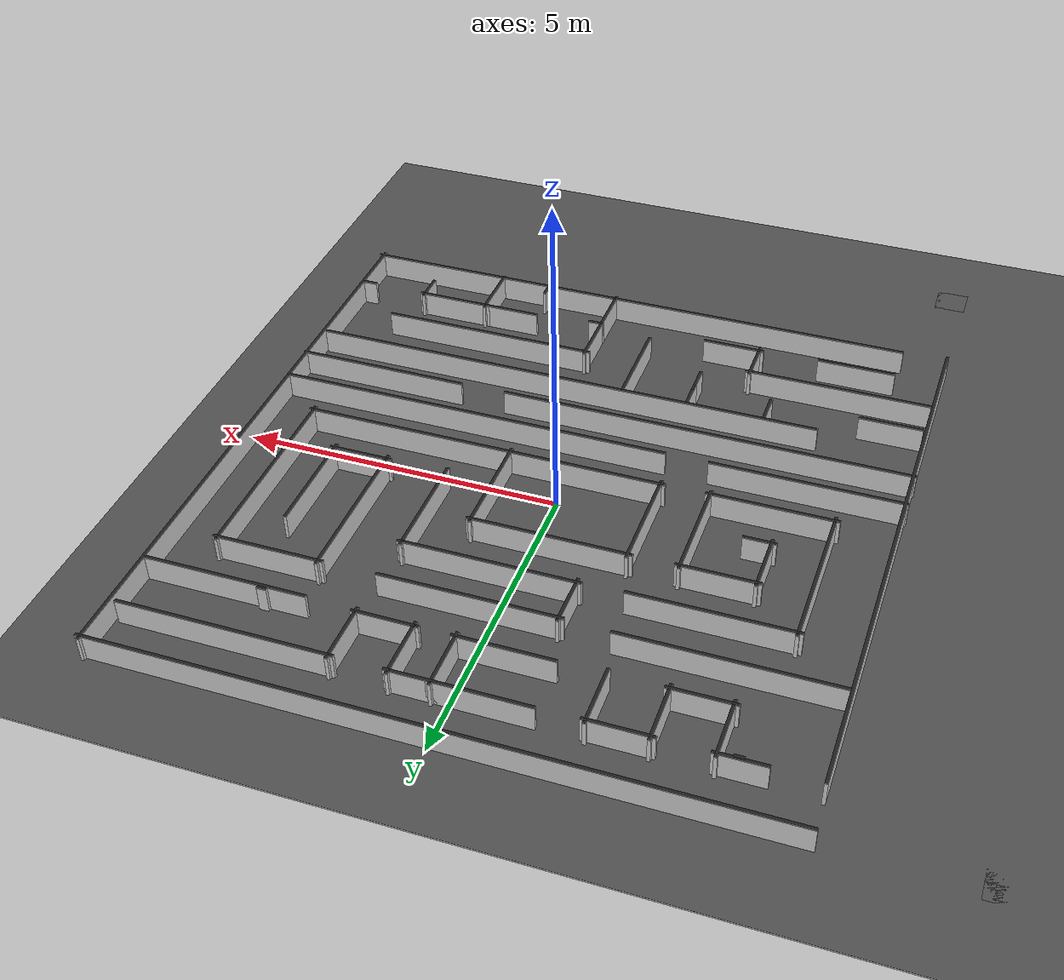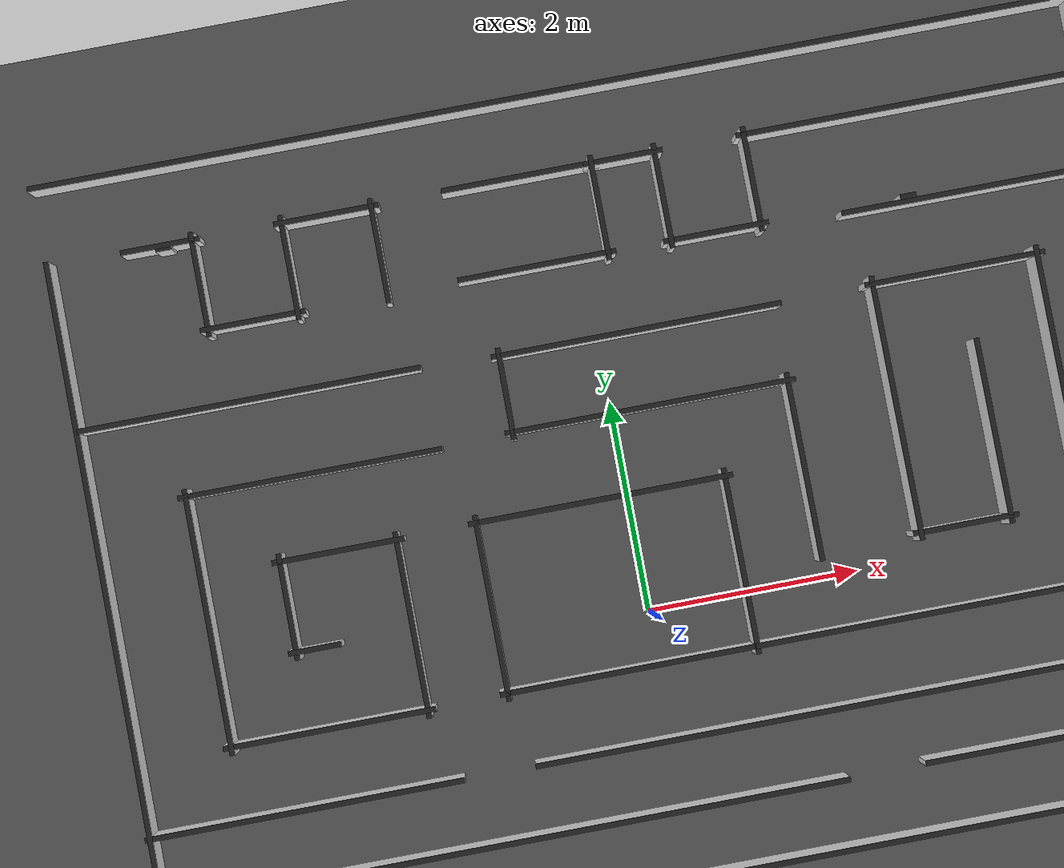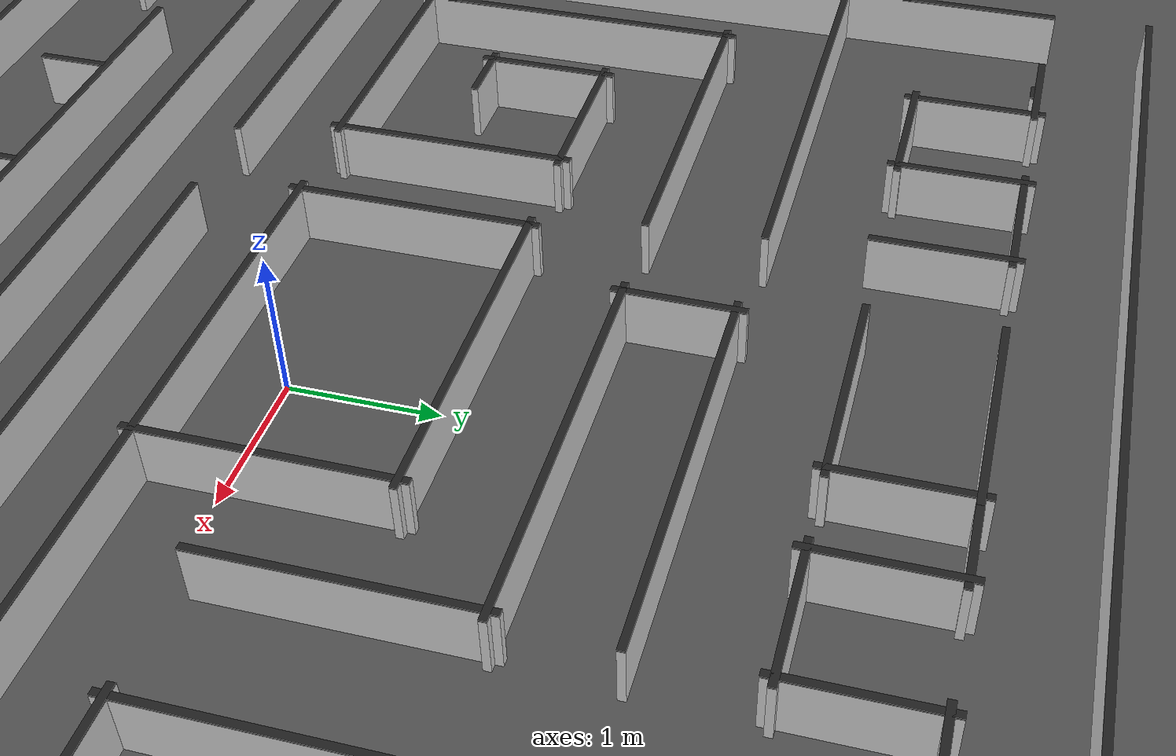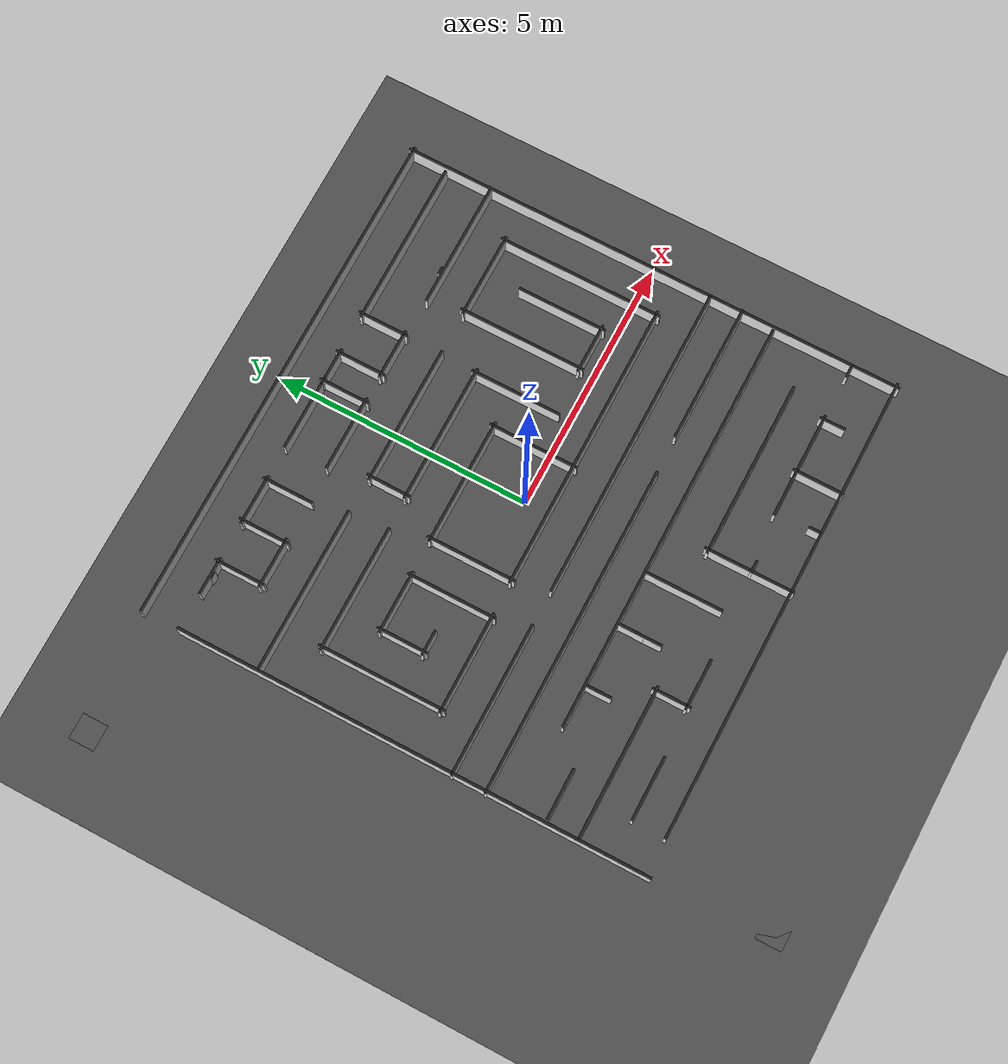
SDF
<sdf version="1.6">
 <world name="default">
  <light name="sun" type="directional">
   <pose>0 0 10 0 -0 0</pose>
   <diffuse>0.8 0.8 0.8 1</diffuse>
   <specular>0.1 0.1 0.1 1</specular>
   <attenuation>
    <range>1000</range>
    <constant>0.9</constant>
    <linear>0.01</linear>
    <quadratic>0.001</quadratic>
   </attenuation>
   <direction>-0.5 0.5 -1</direction>
  </light>
  <model name="ground_plane">
   <static>1</static>
   <link name="link">
    <collision name="collision">
     <geometry><plane><normal>0 0 1</normal><size>100 100</size></plane></geometry>
     <surface><friction><ode><mu>100</mu><mu2>50</mu2></ode></friction></surface>
    </collision>
    <visual name="visual">
     <cast_shadows>0</cast_shadows>
     <geometry><plane><normal>0 0 1</normal><size>100 100</size></plane></geometry>
     <material>
      <script><uri>file://media/materials/scripts/gazebo.material</uri><name>Gazebo/Grey</name></script>
     </material>
    </visual>
   </link>
  </model>
  <gravity>0 0 -9.8</gravity>
  <magnetic_field>6e-06 2.3e-05 -4.2e-05</magnetic_field>
  <atmosphere type="adiabatic"/>
  <physics name="default_physics" default="0" type="ode">
   <max_step_size>0.001</max_step_size>
   <real_time_factor>1</real_time_factor>
   <real_time_update_rate>1000</real_time_update_rate>
  </physics>
  <scene><ambient>0.4 0.4 0.4 1</ambient><background>0.7 0.7 0.7 1</background><shadows>1</shadows></scene>
  <spherical_coordinates>
   <surface_model>EARTH_WGS84</surface_model>
   <latitude_deg>0</latitude_deg>
   <longitude_deg>0</longitude_deg>
   <elevation>0</elevation>
   <heading_deg>0</heading_deg>
  </spherical_coordinates>
  <model name="10x10_maze_2_body">
   <link name="Wall_102">
    <collision name="Wall_102_Collision">
     <geometry><box><size>3.25 0.05 0.4</size></box></geometry>
     <pose>0 0 0.2 0 -0 0</pose>
    </collision>
    <visual name="Wall_102_Visual">
     <pose>0 0 0.2 0 -0 0</pose>
     <geometry><box><size>3.25 0.05 0.4</size></box></geometry>
     <material>
      <script><uri>file://media/materials/scripts/gazebo.material</uri><name>Gazebo/White</name></script>
      <ambient>1 1 1 1</ambient>
     </material>
    </visual>
    <pose>4.15557 1.06055 0 0 0 -1.5708</pose>
   </link>
   <link name="Wall_103">
    <collision name="Wall_103_Collision">
     <geometry><box><size>5.75 0.05 0.4</size></box></geometry>
     <pose>0 0 0.2 0 -0 0</pose>
    </collision>
    <visual name="Wall_103_Visual">
     <pose>0 0 0.2 0 -0 0</pose>
     <geometry><box><size>5.75 0.05 0.4</size></box></geometry>
     <material>
      <script><uri>file://media/materials/scripts/gazebo.material</uri><name>Gazebo/White</name></script>
      <ambient>1 1 1 1</ambient>
     </material>
    </visual>
    <pose>1.35556 -0.489447 0 0 -0 3.14159</pose>
   </link>
   <link name="Wall_104">
    <collision name="Wall_104_Collision">
     <geometry><box><size>1.75 0.05 0.4</size></box></geometry>
     <pose>0 0 0.2 0 -0 0</pose>
    </collision>
    <visual name="Wall_104_Visual">
     <pose>0 0 0.2 0 -0 0</pose>
     <geometry><box><size>1.75 0.05 0.4</size></box></geometry>
     <material>
      <script><uri>file://media/materials/scripts/gazebo.material</uri><name>Gazebo/White</name></script>
      <ambient>1 1 1 1</ambient>
     </material>
    </visual>
    <pose>-1.44443 0.310553 0 0 -0 1.5708</pose>
   </link>
   <link name="Wall_105">
    <collision name="Wall_105_Collision">
     <geometry><box><size>2.5 0.05 0.4</size></box></geometry>
     <pose>0 0 0.2 0 -0 0</pose>
    </collision>
    <visual name="Wall_105_Visual">
     <pose>0 0 0.2 0 -0 0</pose>
     <geometry><box><size>2.5 0.05 0.4</size></box></geometry>
     <material>
      <script><uri>file://media/materials/scripts/gazebo.material</uri><name>Gazebo/White</name></script>
      <ambient>1 1 1 1</ambient>
     </material>
    </visual>
    <pose>-0.269435 1.11055 0 0 -0 0</pose>
   </link>
   <link name="Wall_106">
    <collision name="Wall_106_Collision">
     <geometry><box><size>1.75 0.05 0.4</size></box></geometry>
     <pose>0 0 0.2 0 -0 0</pose>
    </collision>
    <visual name="Wall_106_Visual">
     <pose>0 0 0.2 0 -0 0</pose>
     <geometry><box><size>1.75 0.05 0.4</size></box></geometry>
     <material>
      <script><uri>file://media/materials/scripts/gazebo.material</uri><name>Gazebo/White</name></script>
      <ambient>1 1 1 1</ambient>
     </material>
    </visual>
    <pose>0.905565 0.310553 0 0 0 -1.5708</pose>
   </link>
   <link name="Wall_110">
    <collision name="Wall_110_Collision">
     <geometry><box><size>0.870658 0.05 0.4</size></box></geometry>
     <pose>0 0 0.2 0 -0 0</pose>
    </collision>
    <visual name="Wall_110_Visual">
     <pose>0 0 0.2 0 -0 0</pose>
     <geometry><box><size>0.870658 0.05 0.4</size></box></geometry>
     <material>
      <script><uri>file://media/materials/scripts/gazebo.material</uri><name>Gazebo/White</name></script>
      <ambient>1 1 1 1</ambient>
     </material>
    </visual>
    <pose>-0.950482 2.23502 0 0 -0 1.56348</pose>
   </link>
   <link name="Wall_114">
    <collision name="Wall_114_Collision">
     <geometry><box><size>2.75 0.05 0.4</size></box></geometry>
     <pose>0 0 0.2 0 -0 0</pose>
    </collision>
    <visual name="Wall_114_Visual">
     <pose>0 0 0.2 0 -0 0</pose>
     <geometry><box><size>2.75 0.05 0.4</size></box></geometry>
     <material>
      <script><uri>file://media/materials/scripts/gazebo.material</uri><name>Gazebo/White</name></script>
      <ambient>1 1 1 1</ambient>
     </material>
    </visual>
    <pose>0.346883 1.87471 0 0 -0 0</pose>
   </link>
   <link name="Wall_115">
    <collision name="Wall_115_Collision">
     <geometry><box><size>1.78042 0.05 0.4</size></box></geometry>
     <pose>0 0 0.2 0 -0 0</pose>
    </collision>
    <visual name="Wall_115_Visual">
     <pose>0 0 0.2 0 -0 0</pose>
     <geometry><box><size>1.78042 0.05 0.4</size></box></geometry>
     <material>
      <script><uri>file://media/materials/scripts/gazebo.material</uri><name>Gazebo/White</name></script>
      <ambient>1 1 1 1</ambient>
     </material>
    </visual>
    <pose>1.64688 1.0595 0 0 0 -1.5708</pose>
   </link>
   <link name="Wall_120">
    <collision name="Wall_120_Collision">
     <geometry><box><size>2.5 0.05 0.4</size></box></geometry>
     <pose>0 0 0.2 0 -0 0</pose>
    </collision>
    <visual name="Wall_120_Visual">
     <pose>0 0 0.2 0 -0 0</pose>
     <geometry><box><size>2.5 0.05 0.4</size></box></geometry>
     <material>
      <script><uri>file://media/materials/scripts/gazebo.material</uri><name>Gazebo/White</name></script>
      <ambient>1 1 1 1</ambient>
     </material>
    </visual>
    <pose>2.59579 1.43555 0 0 0 -1.5708</pose>
   </link>
   <link name="Wall_121">
    <collision name="Wall_121_Collision">
     <geometry><box><size>1 0.05 0.4</size></box></geometry>
     <pose>0 0 0.2 0 -0 0</pose>
    </collision>
    <visual name="Wall_121_Visual">
     <pose>0 0 0.2 0 -0 0</pose>
     <geometry><box><size>1 0.05 0.4</size></box></geometry>
     <material>
      <script><uri>file://media/materials/scripts/gazebo.material</uri><name>Gazebo/White</name></script>
      <ambient>1 1 1 1</ambient>
     </material>
    </visual>
    <pose>3.02079 0.260553 0 0 -0 0</pose>
   </link>
   <link name="Wall_122">
    <collision name="Wall_122_Collision">
     <geometry><box><size>1.75 0.05 0.4</size></box></geometry>
     <pose>0 0 0.2 0 -0 0</pose>
    </collision>
    <visual name="Wall_122_Visual">
     <pose>0 0 0.2 0 -0 0</pose>
     <geometry><box><size>1.75 0.05 0.4</size></box></geometry>
     <material>
      <script><uri>file://media/materials/scripts/gazebo.material</uri><name>Gazebo/White</name></script>
      <ambient>1 1 1 1</ambient>
     </material>
    </visual>
    <pose>3.44579 1.06055 0 0 -0 1.5708</pose>
   </link>
   <link name="Wall_124">
    <collision name="Wall_124_Collision">
     <geometry><box><size>2.5 0.05 0.4</size></box></geometry>
     <pose>0 0 0.2 0 -0 0</pose>
    </collision>
    <visual name="Wall_124_Visual">
     <pose>0 0 0.2 0 -0 0</pose>
     <geometry><box><size>2.5 0.05 0.4</size></box></geometry>
     <material>
      <script><uri>file://media/materials/scripts/gazebo.material</uri><name>Gazebo/White</name></script>
      <ambient>1 1 1 1</ambient>
     </material>
    </visual>
    <pose>-2.87335 1.84429 0 0 -0 3.14159</pose>
   </link>
   <link name="Wall_128">
    <collision name="Wall_128_Collision">
     <geometry><box><size>2.5 0.05 0.4</size></box></geometry>
     <pose>0 0 0.2 0 -0 0</pose>
    </collision>
    <visual name="Wall_128_Visual">
     <pose>0 0 0.2 0 -0 0</pose>
     <geometry><box><size>2.5 0.05 0.4</size></box></geometry>
     <material>
      <script><uri>file://media/materials/scripts/gazebo.material</uri><name>Gazebo/White</name></script>
      <ambient>1 1 1 1</ambient>
     </material>
    </visual>
    <pose>-4.04835 0.669288 0 0 0 -1.5708</pose>
   </link>
   <link name="Wall_129">
    <collision name="Wall_129_Collision">
     <geometry><box><size>2 0.05 0.4</size></box></geometry>
     <pose>0 0 0.2 0 -0 0</pose>
    </collision>
    <visual name="Wall_129_Visual">
     <pose>0 0 0.2 0 -0 0</pose>
     <geometry><box><size>2 0.05 0.4</size></box></geometry>
     <material>
      <script><uri>file://media/materials/scripts/gazebo.material</uri><name>Gazebo/White</name></script>
      <ambient>1 1 1 1</ambient>
     </material>
    </visual>
    <pose>-3.12335 -0.505712 0 0 -0 0</pose>
   </link>
   <link name="Wall_130">
    <collision name="Wall_130_Collision">
     <geometry><box><size>1.75 0.05 0.4</size></box></geometry>
     <pose>0 0 0.2 0 -0 0</pose>
    </collision>
    <visual name="Wall_130_Visual">
     <pose>0 0 0.2 0 -0 0</pose>
     <geometry><box><size>1.75 0.05 0.4</size></box></geometry>
     <material>
      <script><uri>file://media/materials/scripts/gazebo.material</uri><name>Gazebo/White</name></script>
      <ambient>1 1 1 1</ambient>
     </material>
    </visual>
    <pose>-2.19835 0.294288 0 0 -0 1.5708</pose>
   </link>
   <link name="Wall_131">
    <collision name="Wall_131_Collision">
     <geometry><box><size>1.25 0.05 0.4</size></box></geometry>
     <pose>0 0 0.2 0 -0 0</pose>
    </collision>
    <visual name="Wall_131_Visual">
     <pose>0 0 0.2 0 -0 0</pose>
     <geometry><box><size>1.25 0.05 0.4</size></box></geometry>
     <material>
      <script><uri>file://media/materials/scripts/gazebo.material</uri><name>Gazebo/White</name></script>
      <ambient>1 1 1 1</ambient>
     </material>
    </visual>
    <pose>-2.74835 1.09429 0 0 -0 3.14159</pose>
   </link>
   <link name="Wall_132">
    <collision name="Wall_132_Collision">
     <geometry><box><size>1 0.05 0.4</size></box></geometry>
     <pose>0 0 0.2 0 -0 0</pose>
    </collision>
    <visual name="Wall_132_Visual">
     <pose>0 0 0.2 0 -0 0</pose>
     <geometry><box><size>1 0.05 0.4</size></box></geometry>
     <material>
      <script><uri>file://media/materials/scripts/gazebo.material</uri><name>Gazebo/White</name></script>
      <ambient>1 1 1 1</ambient>
     </material>
    </visual>
    <pose>-3.29834 0.669288 0 0 0 -1.5708</pose>
   </link>
   <link name="Wall_133">
    <collision name="Wall_133_Collision">
     <geometry><box><size>0.5 0.05 0.4</size></box></geometry>
     <pose>0 0 0.2 0 -0 0</pose>
    </collision>
    <visual name="Wall_133_Visual">
     <pose>0 0 0.2 0 -0 0</pose>
     <geometry><box><size>0.5 0.05 0.4</size></box></geometry>
     <material>
      <script><uri>file://media/materials/scripts/gazebo.material</uri><name>Gazebo/White</name></script>
      <ambient>1 1 1 1</ambient>
     </material>
    </visual>
    <pose>-3.12335 0.244288 0 0 -0 0</pose>
   </link>
   <link name="Wall_135">
    <collision name="Wall_135_Collision">
     <geometry><box><size>3 0.05 0.4</size></box></geometry>
     <pose>0 0 0.2 0 -0 0</pose>
    </collision>
    <visual name="Wall_135_Visual">
     <pose>0 0 0.2 0 -0 0</pose>
     <geometry><box><size>3 0.05 0.4</size></box></geometry>
     <material>
      <script><uri>file://media/materials/scripts/gazebo.material</uri><name>Gazebo/White</name></script>
      <ambient>1 1 1 1</ambient>
     </material>
    </visual>
    <pose>-3.48239 -1.19746 0 0 -0 0</pose>
   </link>
   <link name="Wall_137">
    <collision name="Wall_137_Collision">
     <geometry><box><size>6.25 0.05 0.4</size></box></geometry>
     <pose>0 0 0.2 0 -0 0</pose>
    </collision>
    <visual name="Wall_137_Visual">
     <pose>0 0 0.2 0 -0 0</pose>
     <geometry><box><size>6.25 0.05 0.4</size></box></geometry>
     <material>
      <script><uri>file://media/materials/scripts/gazebo.material</uri><name>Gazebo/White</name></script>
      <ambient>1 1 1 1</ambient>
     </material>
    </visual>
    <pose>1.80792 -1.19746 0 0 -0 0</pose>
   </link>
   <link name="Wall_139">
    <collision name="Wall_139_Collision">
     <geometry><box><size>6.5 0.05 0.4</size></box></geometry>
     <pose>0 0 0.2 0 -0 0</pose>
    </collision>
    <visual name="Wall_139_Visual">
     <pose>0 0 0.2 0 -0 0</pose>
     <geometry><box><size>6.5 0.05 0.4</size></box></geometry>
     <material>
      <script><uri>file://media/materials/scripts/gazebo.material</uri><name>Gazebo/White</name></script>
      <ambient>1 1 1 1</ambient>
     </material>
    </visual>
    <pose>-1.73239 -1.85144 0 0 -0 0</pose>
   </link>
   <link name="Wall_141">
    <collision name="Wall_141_Collision">
     <geometry><box><size>2.75 0.05 0.4</size></box></geometry>
     <pose>0 0 0.2 0 -0 0</pose>
    </collision>
    <visual name="Wall_141_Visual">
     <pose>0 0 0.2 0 -0 0</pose>
     <geometry><box><size>2.75 0.05 0.4</size></box></geometry>
     <material>
      <script><uri>file://media/materials/scripts/gazebo.material</uri><name>Gazebo/White</name></script>
      <ambient>1 1 1 1</ambient>
     </material>
    </visual>
    <pose>3.60156 -1.83623 0 0 -0 0</pose>
   </link>
   <link name="Wall_145">
    <collision name="Wall_145_Collision">
     <geometry><box><size>8.25 0.05 0.4</size></box></geometry>
     <pose>0 0 0.2 0 -0 0</pose>
    </collision>
    <visual name="Wall_145_Visual">
     <pose>0 0 0.2 0 -0 0</pose>
     <geometry><box><size>8.25 0.05 0.4</size></box></geometry>
     <material>
      <script><uri>file://media/materials/scripts/gazebo.material</uri><name>Gazebo/White</name></script>
      <ambient>1 1 1 1</ambient>
     </material>
    </visual>
    <pose>0.769944 -2.49021 0 0 -0 0</pose>
   </link>
   <link name="Wall_153">
    <collision name="Wall_153_Collision">
     <geometry><box><size>1.25 0.05 0.4</size></box></geometry>
     <pose>0 0 0.2 0 -0 0</pose>
    </collision>
    <visual name="Wall_153_Visual">
     <pose>0 0 0.2 0 -0 0</pose>
     <geometry><box><size>1.25 0.05 0.4</size></box></geometry>
     <material>
      <script><uri>file://media/materials/scripts/gazebo.material</uri><name>Gazebo/White</name></script>
      <ambient>1 1 1 1</ambient>
     </material>
    </visual>
    <pose>-3.59695 -4.26963 0 0 -0 0</pose>
   </link>
   <link name="Wall_156">
    <collision name="Wall_156_Collision">
     <geometry><box><size>3 0.05 0.4</size></box></geometry>
     <pose>0 0 0.2 0 -0 0</pose>
    </collision>
    <visual name="Wall_156_Visual">
     <pose>0 0 0.2 0 -0 0</pose>
     <geometry><box><size>3 0.05 0.4</size></box></geometry>
     <material>
      <script><uri>file://media/materials/scripts/gazebo.material</uri><name>Gazebo/White</name></script>
      <ambient>1 1 1 1</ambient>
     </material>
    </visual>
    <pose>-3.43676 -3.61565 0 0 -0 0</pose>
   </link>
   <link name="Wall_157">
    <collision name="Wall_157_Collision">
     <geometry><box><size>0.75 0.05 0.4</size></box></geometry>
     <pose>0 0 0.2 0 -0 0</pose>
    </collision>
    <visual name="Wall_157_Visual">
     <pose>0 0 0.2 0 -0 0</pose>
     <geometry><box><size>0.75 0.05 0.4</size></box></geometry>
     <material>
      <script><uri>file://media/materials/scripts/gazebo.material</uri><name>Gazebo/White</name></script>
      <ambient>1 1 1 1</ambient>
     </material>
    </visual>
    <pose>-2.01177 -3.91565 0 0 0 -1.5708</pose>
   </link>
   <link name="Wall_162">
    <collision name="Wall_162_Collision">
     <geometry><box><size>1 0.05 0.4</size></box></geometry>
     <pose>0 0 0.2 0 -0 0</pose>
    </collision>
    <visual name="Wall_162_Visual">
     <pose>0 0 0.2 0 -0 0</pose>
     <geometry><box><size>1 0.05 0.4</size></box></geometry>
     <material>
      <script><uri>file://media/materials/scripts/gazebo.material</uri><name>Gazebo/White</name></script>
      <ambient>1 1 1 1</ambient>
     </material>
    </visual>
    <pose>-4.39114 -2.99209 0 0 -0 0</pose>
   </link>
   <link name="Wall_164">
    <collision name="Wall_164_Collision">
     <geometry><box><size>0.5 0.05 0.4</size></box></geometry>
     <pose>0 0 0.2 0 -0 0</pose>
    </collision>
    <visual name="Wall_164_Visual">
     <pose>0 0 0.2 0 -0 0</pose>
     <geometry><box><size>0.5 0.05 0.4</size></box></geometry>
     <material>
      <script><uri>file://media/materials/scripts/gazebo.material</uri><name>Gazebo/White</name></script>
      <ambient>1 1 1 1</ambient>
     </material>
    </visual>
    <pose>-2.50441 -2.75646 0 0 0 -1.5708</pose>
   </link>
   <link name="Wall_166">
    <collision name="Wall_166_Collision">
     <geometry><box><size>0.5 0.05 0.4</size></box></geometry>
     <pose>0 0 0.2 0 -0 0</pose>
    </collision>
    <visual name="Wall_166_Visual">
     <pose>0 0 0.2 0 -0 0</pose>
     <geometry><box><size>0.5 0.05 0.4</size></box></geometry>
     <material>
      <script><uri>file://media/materials/scripts/gazebo.material</uri><name>Gazebo/White</name></script>
      <ambient>1 1 1 1</ambient>
     </material>
    </visual>
    <pose>-1.2725 -2.75646 0 0 0 -1.5708</pose>
   </link>
   <link name="Wall_167">
    <collision name="Wall_167_Collision">
     <geometry><box><size>0.5 0.05 0.4</size></box></geometry>
     <pose>0 0 0.2 0 -0 0</pose>
    </collision>
    <visual name="Wall_167_Visual">
     <pose>0 0 0.2 0 -0 0</pose>
     <geometry><box><size>0.5 0.05 0.4</size></box></geometry>
     <material>
      <script><uri>file://media/materials/scripts/gazebo.material</uri><name>Gazebo/White</name></script>
      <ambient>1 1 1 1</ambient>
     </material>
    </visual>
    <pose>-1.2725 -3.10646 0 0 0 -1.5708</pose>
   </link>
   <link name="Wall_169">
    <collision name="Wall_169_Collision">
     <geometry><box><size>1.5 0.05 0.4</size></box></geometry>
     <pose>0 0 0.2 0 -0 0</pose>
    </collision>
    <visual name="Wall_169_Visual">
     <pose>0 0 0.2 0 -0 0</pose>
     <geometry><box><size>1.5 0.05 0.4</size></box></geometry>
     <material>
      <script><uri>file://media/materials/scripts/gazebo.material</uri><name>Gazebo/White</name></script>
      <ambient>1 1 1 1</ambient>
     </material>
    </visual>
    <pose>-0.223097 -3.25646 0 0 0 -1.5708</pose>
   </link>
   <link name="Wall_171">
    <collision name="Wall_171_Collision">
     <geometry><box><size>1 0.05 0.4</size></box></geometry>
     <pose>0 0 0.2 0 -0 0</pose>
    </collision>
    <visual name="Wall_171_Visual">
     <pose>0 0 0.2 0 -0 0</pose>
     <geometry><box><size>1 0.05 0.4</size></box></geometry>
     <material>
      <script><uri>file://media/materials/scripts/gazebo.material</uri><name>Gazebo/White</name></script>
      <ambient>1 1 1 1</ambient>
     </material>
    </visual>
    <pose>-1.58677 -4.21565 0 0 -0 0</pose>
   </link>
   <link name="Wall_173">
    <collision name="Wall_173_Collision">
     <geometry><box><size>1.75 0.05 0.4</size></box></geometry>
     <pose>0 0 0.2 0 -0 0</pose>
    </collision>
    <visual name="Wall_173_Visual">
     <pose>0 0 0.2 0 -0 0</pose>
     <geometry><box><size>1.75 0.05 0.4</size></box></geometry>
     <material>
      <script><uri>file://media/materials/scripts/gazebo.material</uri><name>Gazebo/White</name></script>
      <ambient>1 1 1 1</ambient>
     </material>
    </visual>
    <pose>0.659011 -4.09319 0 0 -0 1.5708</pose>
   </link>
   <link name="Wall_174">
    <collision name="Wall_174_Collision">
     <geometry><box><size>3.5 0.05 0.4</size></box></geometry>
     <pose>0 0 0.2 0 -0 0</pose>
    </collision>
    <visual name="Wall_174_Visual">
     <pose>0 0 0.2 0 -0 0</pose>
     <geometry><box><size>3.5 0.05 0.4</size></box></geometry>
     <material>
      <script><uri>file://media/materials/scripts/gazebo.material</uri><name>Gazebo/White</name></script>
      <ambient>1 1 1 1</ambient>
     </material>
    </visual>
    <pose>2.33401 -3.29319 0 0 -0 0</pose>
   </link>
   <link name="Wall_176">
    <collision name="Wall_176_Collision">
     <geometry><box><size>1 0.05 0.4</size></box></geometry>
     <pose>0 0 0.2 0 -0 0</pose>
    </collision>
    <visual name="Wall_176_Visual">
     <pose>0 0 0.2 0 -0 0</pose>
     <geometry><box><size>1 0.05 0.4</size></box></geometry>
     <material>
      <script><uri>file://media/materials/scripts/gazebo.material</uri><name>Gazebo/White</name></script>
      <ambient>1 1 1 1</ambient>
     </material>
    </visual>
    <pose>2.68177 -4.45298 0 0 -0 1.5708</pose>
   </link>
   <link name="Wall_186">
    <collision name="Wall_186_Collision">
     <geometry><box><size>0.25 0.05 0.4</size></box></geometry>
     <pose>0 0 0.2 0 -0 0</pose>
    </collision>
    <visual name="Wall_186_Visual">
     <pose>0 0 0.2 0 -0 0</pose>
     <geometry><box><size>0.25 0.05 0.4</size></box></geometry>
     <material>
      <script><uri>file://media/materials/scripts/gazebo.material</uri><name>Gazebo/White</name></script>
      <ambient>1 1 1 1</ambient>
     </material>
    </visual>
    <pose>0.754637 -4.13275 0 0 -0 0</pose>
   </link>
   <link name="Wall_188">
    <collision name="Wall_188_Collision">
     <geometry><box><size>0.25 0.05 0.4</size></box></geometry>
     <pose>0 0 0.2 0 -0 0</pose>
    </collision>
    <visual name="Wall_188_Visual">
     <pose>0 0 0.2 0 -0 0</pose>
     <geometry><box><size>0.25 0.05 0.4</size></box></geometry>
     <material>
      <script><uri>file://media/materials/scripts/gazebo.material</uri><name>Gazebo/White</name></script>
      <ambient>1 1 1 1</ambient>
     </material>
    </visual>
    <pose>4.80663 -4.0415 0 0 -0 3.14159</pose>
   </link>
   <link name="Wall_190">
    <collision name="Wall_190_Collision">
     <geometry><box><size>1 0.05 0.4</size></box></geometry>
     <pose>0 0 0.2 0 -0 0</pose>
    </collision>
    <visual name="Wall_190_Visual">
     <pose>0 0 0.2 0 -0 0</pose>
     <geometry><box><size>1 0.05 0.4</size></box></geometry>
     <material>
      <script><uri>file://media/materials/scripts/gazebo.material</uri><name>Gazebo/White</name></script>
      <ambient>1 1 1 1</ambient>
     </material>
    </visual>
    <pose>2.25677 -4.02798 0 0 -0 3.14159</pose>
   </link>
   <link name="Wall_192">
    <collision name="Wall_192_Collision">
     <geometry><box><size>1.25 0.05 0.4</size></box></geometry>
     <pose>0 0 0.2 0 -0 0</pose>
    </collision>
    <visual name="Wall_192_Visual">
     <pose>0 0 0.2 0 -0 0</pose>
     <geometry><box><size>1.25 0.05 0.4</size></box></geometry>
     <material>
      <script><uri>file://media/materials/scripts/gazebo.material</uri><name>Gazebo/White</name></script>
      <ambient>1 1 1 1</ambient>
     </material>
    </visual>
    <pose>3.23177 -4.02798 0 0 -0 0</pose>
   </link>
   <link name="Wall_194">
    <collision name="Wall_194_Collision">
     <geometry><box><size>0.25 0.05 0.4</size></box></geometry>
     <pose>0 0 0.2 0 -0 0</pose>
    </collision>
    <visual name="Wall_194_Visual">
     <pose>0 0 0.2 0 -0 0</pose>
     <geometry><box><size>0.25 0.05 0.4</size></box></geometry>
     <material>
      <script><uri>file://media/materials/scripts/gazebo.material</uri><name>Gazebo/White</name></script>
      <ambient>1 1 1 1</ambient>
     </material>
    </visual>
    <pose>1.85349 -4.78989 0 0 -0 1.5708</pose>
   </link>
   <link name="Wall_196">
    <collision name="Wall_196_Collision">
     <geometry><box><size>0.5 0.05 0.4</size></box></geometry>
     <pose>0 0 0.2 0 -0 0</pose>
    </collision>
    <visual name="Wall_196_Visual">
     <pose>0 0 0.2 0 -0 0</pose>
     <geometry><box><size>0.5 0.05 0.4</size></box></geometry>
     <material>
      <script><uri>file://media/materials/scripts/gazebo.material</uri><name>Gazebo/White</name></script>
      <ambient>1 1 1 1</ambient>
     </material>
    </visual>
    <pose>3.78178 -4.20298 0 0 0 -1.5708</pose>
   </link>
   <link name="Wall_26">
    <collision name="Wall_26_Collision">
     <geometry><box><size>10 0.05 0.4</size></box></geometry>
     <pose>0 0 0.2 0 -0 0</pose>
    </collision>
    <visual name="Wall_26_Visual">
     <pose>0 0 0.2 0 -0 0</pose>
     <geometry><box><size>10 0.05 0.4</size></box></geometry>
     <material>
      <script><uri>file://media/materials/scripts/gazebo.material</uri><name>Gazebo/White</name></script>
      <ambient>1 1 1 1</ambient>
     </material>
    </visual>
    <pose>0.011565 4.93839 0 0 -0 0</pose>
   </link>
   <link name="Wall_27">
    <collision name="Wall_27_Collision">
     <geometry><box><size>10 0.05 0.4</size></box></geometry>
     <pose>0 0 0.2 0 -0 0</pose>
    </collision>
    <visual name="Wall_27_Visual">
     <pose>0 0 0.2 0 -0 0</pose>
     <geometry><box><size>10 0.05 0.4</size></box></geometry>
     <material>
      <script><uri>file://media/materials/scripts/gazebo.material</uri><name>Gazebo/White</name></script>
      <ambient>1 1 1 1</ambient>
     </material>
    </visual>
    <pose>4.93656 0.013385 0 0 0 -1.5708</pose>
   </link>
   <link name="Wall_30">
    <collision name="Wall_30_Collision">
     <geometry><box><size>9.25 0.05 0.4</size></box></geometry>
     <pose>0 0 0.2 0 -0 0</pose>
    </collision>
    <visual name="Wall_30_Visual">
     <pose>0 0 0.2 0 -0 0</pose>
     <geometry><box><size>9.25 0.05 0.4</size></box></geometry>
     <material>
      <script><uri>file://media/materials/scripts/gazebo.material</uri><name>Gazebo/White</name></script>
      <ambient>1 1 1 1</ambient>
     </material>
    </visual>
    <pose>0.386565 -4.91162 0 0 -0 3.14159</pose>
   </link>
   <link name="Wall_32">
    <collision name="Wall_32_Collision">
     <geometry><box><size>9.25 0.05 0.4</size></box></geometry>
     <pose>0 0 0.2 0 -0 0</pose>
    </collision>
    <visual name="Wall_32_Visual">
     <pose>0 0 0.2 0 -0 0</pose>
     <geometry><box><size>9.25 0.05 0.4</size></box></geometry>
     <material>
      <script><uri>file://media/materials/scripts/gazebo.material</uri><name>Gazebo/White</name></script>
      <ambient>1 1 1 1</ambient>
     </material>
    </visual>
    <pose>-4.93656 -0.388385 0 0 -0 1.5708</pose>
   </link>
   <link name="Wall_36">
    <collision name="Wall_36_Collision">
     <geometry><box><size>0.15 0.05 0.4</size></box></geometry>
     <pose>0 0 0.2 0 -0 0</pose>
    </collision>
    <visual name="Wall_36_Visual">
     <pose>0 0 0.2 0 -0 0</pose>
     <geometry><box><size>0.15 0.05 0.4</size></box></geometry>
     <material>
      <script><uri>file://media/materials/scripts/gazebo.material</uri><name>Gazebo/White</name></script>
      <ambient>1 1 1 1</ambient>
     </material>
    </visual>
    <pose>-3.83656 4.16162 0 0 -0 0</pose>
   </link>
   <link name="Wall_50">
    <collision name="Wall_50_Collision">
     <geometry><box><size>1 0.05 0.4</size></box></geometry>
     <pose>0 0 0.2 0 -0 0</pose>
    </collision>
    <visual name="Wall_50_Visual">
     <pose>0 0 0.2 0 -0 0</pose>
     <geometry><box><size>1 0.05 0.4</size></box></geometry>
     <material>
      <script><uri>file://media/materials/scripts/gazebo.material</uri><name>Gazebo/White</name></script>
      <ambient>1 1 1 1</ambient>
     </material>
    </visual>
    <pose>-3.13787 3.34011 0 0 -0 0</pose>
   </link>
   <link name="Wall_51">
    <collision name="Wall_51_Collision">
     <geometry><box><size>1 0.05 0.4</size></box></geometry>
     <pose>0 0 0.2 0 -0 0</pose>
    </collision>
    <visual name="Wall_51_Visual">
     <pose>0 0 0.2 0 -0 0</pose>
     <geometry><box><size>1 0.05 0.4</size></box></geometry>
     <material>
      <script><uri>file://media/materials/scripts/gazebo.material</uri><name>Gazebo/White</name></script>
      <ambient>1 1 1 1</ambient>
     </material>
    </visual>
    <pose>-2.71287 3.76511 0 0 -0 1.5708</pose>
   </link>
   <link name="Wall_52">
    <collision name="Wall_52_Collision">
     <geometry><box><size>1 0.05 0.4</size></box></geometry>
     <pose>0 0 0.2 0 -0 0</pose>
    </collision>
    <visual name="Wall_52_Visual">
     <pose>0 0 0.2 0 -0 0</pose>
     <geometry><box><size>1 0.05 0.4</size></box></geometry>
     <material>
      <script><uri>file://media/materials/scripts/gazebo.material</uri><name>Gazebo/White</name></script>
      <ambient>1 1 1 1</ambient>
     </material>
    </visual>
    <pose>-2.28787 4.19011 0 0 -0 0</pose>
   </link>
   <link name="Wall_53">
    <collision name="Wall_53_Collision">
     <geometry><box><size>1 0.05 0.4</size></box></geometry>
     <pose>0 0 0.2 0 -0 0</pose>
    </collision>
    <visual name="Wall_53_Visual">
     <pose>0 0 0.2 0 -0 0</pose>
     <geometry><box><size>1 0.05 0.4</size></box></geometry>
     <material>
      <script><uri>file://media/materials/scripts/gazebo.material</uri><name>Gazebo/White</name></script>
      <ambient>1 1 1 1</ambient>
     </material>
    </visual>
    <pose>-1.86287 3.76511 0 0 0 -1.5708</pose>
   </link>
   <link name="Wall_56">
    <collision name="Wall_56_Collision">
     <geometry><box><size>1.5 0.05 0.4</size></box></geometry>
     <pose>0 0 0.2 0 -0 0</pose>
    </collision>
    <visual name="Wall_56_Visual">
     <pose>0 0 0.2 0 -0 0</pose>
     <geometry><box><size>1.5 0.05 0.4</size></box></geometry>
     <material>
      <script><uri>file://media/materials/scripts/gazebo.material</uri><name>Gazebo/White</name></script>
      <ambient>1 1 1 1</ambient>
     </material>
    </visual>
    <pose>-0.444597 4.2076 0 0 -0 0</pose>
   </link>
   <link name="Wall_57">
    <collision name="Wall_57_Collision">
     <geometry><box><size>1 0.05 0.4</size></box></geometry>
     <pose>0 0 0.2 0 -0 0</pose>
    </collision>
    <visual name="Wall_57_Visual">
     <pose>0 0 0.2 0 -0 0</pose>
     <geometry><box><size>1 0.05 0.4</size></box></geometry>
     <material>
      <script><uri>file://media/materials/scripts/gazebo.material</uri><name>Gazebo/White</name></script>
      <ambient>1 1 1 1</ambient>
     </material>
    </visual>
    <pose>0.230403 3.7826 0 0 0 -1.5708</pose>
   </link>
   <link name="Wall_58">
    <collision name="Wall_58_Collision">
     <geometry><box><size>1.5 0.05 0.4</size></box></geometry>
     <pose>0 0 0.2 0 -0 0</pose>
    </collision>
    <visual name="Wall_58_Visual">
     <pose>0 0 0.2 0 -0 0</pose>
     <geometry><box><size>1.5 0.05 0.4</size></box></geometry>
     <material>
      <script><uri>file://media/materials/scripts/gazebo.material</uri><name>Gazebo/White</name></script>
      <ambient>1 1 1 1</ambient>
     </material>
    </visual>
    <pose>-0.444597 3.3576 0 0 -0 3.14159</pose>
   </link>
   <link name="Wall_64">
    <collision name="Wall_64_Collision">
     <geometry><box><size>0.15 0.05 0.4</size></box></geometry>
     <pose>0 0 0.2 0 -0 0</pose>
    </collision>
    <visual name="Wall_64_Visual">
     <pose>0 0 0.2 0 -0 0</pose>
     <geometry><box><size>0.15 0.05 0.4</size></box></geometry>
     <material>
      <script><uri>file://media/materials/scripts/gazebo.material</uri><name>Gazebo/White</name></script>
      <ambient>1 1 1 1</ambient>
     </material>
    </visual>
    <pose>3.0804 3.3576 0 0 -0 0</pose>
   </link>
   <link name="Wall_70">
    <collision name="Wall_70_Collision">
     <geometry><box><size>0.75 0.05 0.4</size></box></geometry>
     <pose>0 0 0.2 0 -0 0</pose>
    </collision>
    <visual name="Wall_70_Visual">
     <pose>0 0 0.2 0 -0 0</pose>
     <geometry><box><size>0.75 0.05 0.4</size></box></geometry>
     <material>
      <script><uri>file://media/materials/scripts/gazebo.material</uri><name>Gazebo/White</name></script>
      <ambient>1 1 1 1</ambient>
     </material>
    </visual>
    <pose>0.530403 4.2076 0 0 -0 0</pose>
   </link>
   <link name="Wall_71">
    <collision name="Wall_71_Collision">
     <geometry><box><size>1 0.05 0.4</size></box></geometry>
     <pose>0 0 0.2 0 -0 0</pose>
    </collision>
    <visual name="Wall_71_Visual">
     <pose>0 0 0.2 0 -0 0</pose>
     <geometry><box><size>1 0.05 0.4</size></box></geometry>
     <material>
      <script><uri>file://media/materials/scripts/gazebo.material</uri><name>Gazebo/White</name></script>
      <ambient>1 1 1 1</ambient>
     </material>
    </visual>
    <pose>0.830403 3.7826 0 0 0 -1.5708</pose>
   </link>
   <link name="Wall_74">
    <collision name="Wall_74_Collision">
     <geometry><box><size>1 0.05 0.4</size></box></geometry>
     <pose>0 0 0.2 0 -0 0</pose>
    </collision>
    <visual name="Wall_74_Visual">
     <pose>0 0 0.2 0 -0 0</pose>
     <geometry><box><size>1 0.05 0.4</size></box></geometry>
     <material>
      <script><uri>file://media/materials/scripts/gazebo.material</uri><name>Gazebo/White</name></script>
      <ambient>1 1 1 1</ambient>
     </material>
    </visual>
    <pose>1.2554 3.3576 0 0 -0 0</pose>
   </link>
   <link name="Wall_76">
    <collision name="Wall_76_Collision">
     <geometry><box><size>1 0.05 0.4</size></box></geometry>
     <pose>0 0 0.2 0 -0 0</pose>
    </collision>
    <visual name="Wall_76_Visual">
     <pose>0 0 0.2 0 -0 0</pose>
     <geometry><box><size>1 0.05 0.4</size></box></geometry>
     <material>
      <script><uri>file://media/materials/scripts/gazebo.material</uri><name>Gazebo/White</name></script>
      <ambient>1 1 1 1</ambient>
     </material>
    </visual>
    <pose>1.6804 3.7826 0 0 -0 1.5708</pose>
   </link>
   <link name="Wall_77">
    <collision name="Wall_77_Collision">
     <geometry><box><size>3.25 0.05 0.4</size></box></geometry>
     <pose>0 0 0.2 0 -0 0</pose>
    </collision>
    <visual name="Wall_77_Visual">
     <pose>0 0 0.2 0 -0 0</pose>
     <geometry><box><size>3.25 0.05 0.4</size></box></geometry>
     <material>
      <script><uri>file://media/materials/scripts/gazebo.material</uri><name>Gazebo/White</name></script>
      <ambient>1 1 1 1</ambient>
     </material>
    </visual>
    <pose>3.2304 4.2076 0 0 -0 0</pose>
   </link>
   <link name="Wall_79">
    <collision name="Wall_79_Collision">
     <geometry><box><size>2.5 0.05 0.4</size></box></geometry>
     <pose>0 0 0.2 0 -0 0</pose>
    </collision>
    <visual name="Wall_79_Visual">
     <pose>0 0 0.2 0 -0 0</pose>
     <geometry><box><size>2.5 0.05 0.4</size></box></geometry>
     <material>
      <script><uri>file://media/materials/scripts/gazebo.material</uri><name>Gazebo/White</name></script>
      <ambient>1 1 1 1</ambient>
     </material>
    </visual>
    <pose>3.68689 3.31015 0 0 -0 3.14159</pose>
   </link>
   <link name="Wall_85">
    <collision name="Wall_85_Collision">
     <geometry><box><size>1 0.05 0.4</size></box></geometry>
     <pose>0 0 0.2 0 -0 0</pose>
    </collision>
    <visual name="Wall_85_Visual">
     <pose>0 0 0.2 0 -0 0</pose>
     <geometry><box><size>1 0.05 0.4</size></box></geometry>
     <material>
      <script><uri>file://media/materials/scripts/gazebo.material</uri><name>Gazebo/White</name></script>
      <ambient>1 1 1 1</ambient>
     </material>
    </visual>
    <pose>-3.56287 3.76511 0 0 -0 1.5708</pose>
   </link>
   <link name="Wall_86">
    <collision name="Wall_86_Collision">
     <geometry><box><size>0.75 0.05 0.4</size></box></geometry>
     <pose>0 0 0.2 0 -0 0</pose>
    </collision>
    <visual name="Wall_86_Visual">
     <pose>0 0 0.2 0 -0 0</pose>
     <geometry><box><size>0.75 0.05 0.4</size></box></geometry>
     <material>
      <script><uri>file://media/materials/scripts/gazebo.material</uri><name>Gazebo/White</name></script>
      <ambient>1 1 1 1</ambient>
     </material>
    </visual>
    <pose>-3.86287 4.19011 0 0 -0 3.14159</pose>
   </link>
   <link name="Wall_92">
    <collision name="Wall_92_Collision">
     <geometry><box><size>3.25 0.05 0.4</size></box></geometry>
     <pose>0 0 0.2 0 -0 0</pose>
    </collision>
    <visual name="Wall_92_Visual">
     <pose>0 0 0.2 0 -0 0</pose>
     <geometry><box><size>3.25 0.05 0.4</size></box></geometry>
     <material>
      <script><uri>file://media/materials/scripts/gazebo.material</uri><name>Gazebo/White</name></script>
      <ambient>1 1 1 1</ambient>
     </material>
    </visual>
    <pose>-3.3065 2.62576 0 0 -0 0</pose>
   </link>
   <link name="Wall_94">
    <collision name="Wall_94_Collision">
     <geometry><box><size>2.75 0.05 0.4</size></box></geometry>
     <pose>0 0 0.2 0 -0 0</pose>
    </collision>
    <visual name="Wall_94_Visual">
     <pose>0 0 0.2 0 -0 0</pose>
     <geometry><box><size>2.75 0.05 0.4</size></box></geometry>
     <material>
      <script><uri>file://media/materials/scripts/gazebo.material</uri><name>Gazebo/White</name></script>
      <ambient>1 1 1 1</ambient>
     </material>
    </visual>
    <pose>0.352153 2.59534 0 0 -0 0</pose>
   </link>
   <link name="Wall_99">
    <collision name="Wall_99_Collision">
     <geometry><box><size>1.70977 0.05 0.4</size></box></geometry>
     <pose>0 0 0.2 0 -0 0</pose>
    </collision>
    <visual name="Wall_99_Visual">
     <pose>0 0 0.2 0 -0 0</pose>
     <geometry><box><size>1.70977 0.05 0.4</size></box></geometry>
     <material>
      <script><uri>file://media/materials/scripts/gazebo.material</uri><name>Gazebo/White</name></script>
      <ambient>1 1 1 1</ambient>
     </material>
    </visual>
    <pose>3.37568 2.61055 0 0 -0 0</pose>
   </link>
   <static>1</static>
  </model>
  <model name="10x10_maze_2_top">
   <pose>0 0 0.4 0 -0 0</pose>
   <link name="Wall_102">
    <collision name="Wall_102_Collision">
     <geometry><box><size>3.25 0.05 0.01</size></box></geometry>
     <pose>0 0 0.005 0 -0 0</pose>
    </collision>
    <visual name="Wall_102_Visual">
     <pose>0 0 0.005 0 -0 0</pose>
     <geometry><box><size>3.25 0.05 0.01</size></box></geometry>
     <material>
      <script><uri>file://media/materials/scripts/gazebo.material</uri><name>Gazebo/Black</name></script>
      <ambient>0 0 0 1</ambient>
     </material>
    </visual>
    <pose>4.15557 1.06055 0 0 0 -1.5708</pose>
   </link>
   <link name="Wall_103">
    <collision name="Wall_103_Collision">
     <geometry><box><size>5.75 0.05 0.01</size></box></geometry>
     <pose>0 0 0.005 0 -0 0</pose>
    </collision>
    <visual name="Wall_103_Visual">
     <pose>0 0 0.005 0 -0 0</pose>
     <geometry><box><size>5.75 0.05 0.01</size></box></geometry>
     <material>
      <script><uri>file://media/materials/scripts/gazebo.material</uri><name>Gazebo/Black</name></script>
      <ambient>0 0 0 1</ambient>
     </material>
    </visual>
    <pose>1.35556 -0.489447 0 0 -0 3.14159</pose>
   </link>
   <link name="Wall_104">
    <collision name="Wall_104_Collision">
     <geometry><box><size>1.75 0.05 0.01</size></box></geometry>
     <pose>0 0 0.005 0 -0 0</pose>
    </collision>
    <visual name="Wall_104_Visual">
     <pose>0 0 0.005 0 -0 0</pose>
     <geometry><box><size>1.75 0.05 0.01</size></box></geometry>
     <material>
      <script><uri>file://media/materials/scripts/gazebo.material</uri><name>Gazebo/Black</name></script>
      <ambient>0 0 0 1</ambient>
     </material>
    </visual>
    <pose>-1.44443 0.310553 0 0 -0 1.5708</pose>
   </link>
   <link name="Wall_105">
    <collision name="Wall_105_Collision">
     <geometry><box><size>2.5 0.05 0.01</size></box></geometry>
     <pose>0 0 0.005 0 -0 0</pose>
    </collision>
    <visual name="Wall_105_Visual">
     <pose>0 0 0.005 0 -0 0</pose>
     <geometry><box><size>2.5 0.05 0.01</size></box></geometry>
     <material>
      <script><uri>file://media/materials/scripts/gazebo.material</uri><name>Gazebo/Black</name></script>
      <ambient>0 0 0 1</ambient>
     </material>
    </visual>
    <pose>-0.269435 1.11055 0 0 -0 0</pose>
   </link>
   <link name="Wall_106">
    <collision name="Wall_106_Collision">
     <geometry><box><size>1.75 0.05 0.01</size></box></geometry>
     <pose>0 0 0.005 0 -0 0</pose>
    </collision>
    <visual name="Wall_106_Visual">
     <pose>0 0 0.005 0 -0 0</pose>
     <geometry><box><size>1.75 0.05 0.01</size></box></geometry>
     <material>
      <script><uri>file://media/materials/scripts/gazebo.material</uri><name>Gazebo/Black</name></script>
      <ambient>0 0 0 1</ambient>
     </material>
    </visual>
    <pose>0.905565 0.310553 0 0 0 -1.5708</pose>
   </link>
   <link name="Wall_110">
    <collision name="Wall_110_Collision">
     <geometry><box><size>0.870658 0.05 0.01</size></box></geometry>
     <pose>0 0 0.005 0 -0 0</pose>
    </collision>
    <visual name="Wall_110_Visual">
     <pose>0 0 0.005 0 -0 0</pose>
     <geometry><box><size>0.870658 0.05 0.01</size></box></geometry>
     <material>
      <script><uri>file://media/materials/scripts/gazebo.material</uri><name>Gazebo/Black</name></script>
      <ambient>0 0 0 1</ambient>
     </material>
    </visual>
    <pose>-0.950482 2.23502 0 0 -0 1.56348</pose>
   </link>
   <link name="Wall_114">
    <collision name="Wall_114_Collision">
     <geometry><box><size>2.75 0.05 0.01</size></box></geometry>
     <pose>0 0 0.005 0 -0 0</pose>
    </collision>
    <visual name="Wall_114_Visual">
     <pose>0 0 0.005 0 -0 0</pose>
     <geometry><box><size>2.75 0.05 0.01</size></box></geometry>
     <material>
      <script><uri>file://media/materials/scripts/gazebo.material</uri><name>Gazebo/Black</name></script>
      <ambient>0 0 0 1</ambient>
     </material>
    </visual>
    <pose>0.346883 1.87471 0 0 -0 0</pose>
   </link>
   <link name="Wall_115">
    <collision name="Wall_115_Collision">
     <geometry><box><size>1.78042 0.05 0.01</size></box></geometry>
     <pose>0 0 0.005 0 -0 0</pose>
    </collision>
    <visual name="Wall_115_Visual">
     <pose>0 0 0.005 0 -0 0</pose>
     <geometry><box><size>1.78042 0.05 0.01</size></box></geometry>
     <material>
      <script><uri>file://media/materials/scripts/gazebo.material</uri><name>Gazebo/Black</name></script>
      <ambient>0 0 0 1</ambient>
     </material>
    </visual>
    <pose>1.64688 1.0595 0 0 0 -1.5708</pose>
   </link>
   <link name="Wall_120">
    <collision name="Wall_120_Collision">
     <geometry><box><size>2.5 0.05 0.01</size></box></geometry>
     <pose>0 0 0.005 0 -0 0</pose>
    </collision>
    <visual name="Wall_120_Visual">
     <pose>0 0 0.005 0 -0 0</pose>
     <geometry><box><size>2.5 0.05 0.01</size></box></geometry>
     <material>
      <script><uri>file://media/materials/scripts/gazebo.material</uri><name>Gazebo/Black</name></script>
      <ambient>0 0 0 1</ambient>
     </material>
    </visual>
    <pose>2.59579 1.43555 0 0 0 -1.5708</pose>
   </link>
   <link name="Wall_121">
    <collision name="Wall_121_Collision">
     <geometry><box><size>1 0.05 0.01</size></box></geometry>
     <pose>0 0 0.005 0 -0 0</pose>
    </collision>
    <visual name="Wall_121_Visual">
     <pose>0 0 0.005 0 -0 0</pose>
     <geometry><box><size>1 0.05 0.01</size></box></geometry>
     <material>
      <script><uri>file://media/materials/scripts/gazebo.material</uri><name>Gazebo/Black</name></script>
      <ambient>0 0 0 1</ambient>
     </material>
    </visual>
    <pose>3.02079 0.260553 0 0 -0 0</pose>
   </link>
   <link name="Wall_122">
    <collision name="Wall_122_Collision">
     <geometry><box><size>1.75 0.05 0.01</size></box></geometry>
     <pose>0 0 0.005 0 -0 0</pose>
    </collision>
    <visual name="Wall_122_Visual">
     <pose>0 0 0.005 0 -0 0</pose>
     <geometry><box><size>1.75 0.05 0.01</size></box></geometry>
     <material>
      <script><uri>file://media/materials/scripts/gazebo.material</uri><name>Gazebo/Black</name></script>
      <ambient>0 0 0 1</ambient>
     </material>
    </visual>
    <pose>3.44579 1.06055 0 0 -0 1.5708</pose>
   </link>
   <link name="Wall_124">
    <collision name="Wall_124_Collision">
     <geometry><box><size>2.5 0.05 0.01</size></box></geometry>
     <pose>0 0 0.005 0 -0 0</pose>
    </collision>
    <visual name="Wall_124_Visual">
     <pose>0 0 0.005 0 -0 0</pose>
     <geometry><box><size>2.5 0.05 0.01</size></box></geometry>
     <material>
      <script><uri>file://media/materials/scripts/gazebo.material</uri><name>Gazebo/Black</name></script>
      <ambient>0 0 0 1</ambient>
     </material>
    </visual>
    <pose>-2.87335 1.84429 0 0 -0 3.14159</pose>
   </link>
   <link name="Wall_128">
    <collision name="Wall_128_Collision">
     <geometry><box><size>2.5 0.05 0.01</size></box></geometry>
     <pose>0 0 0.005 0 -0 0</pose>
    </collision>
    <visual name="Wall_128_Visual">
     <pose>0 0 0.005 0 -0 0</pose>
     <geometry><box><size>2.5 0.05 0.01</size></box></geometry>
     <material>
      <script><uri>file://media/materials/scripts/gazebo.material</uri><name>Gazebo/Black</name></script>
      <ambient>0 0 0 1</ambient>
     </material>
    </visual>
    <pose>-4.04835 0.669288 0 0 0 -1.5708</pose>
   </link>
   <link name="Wall_129">
    <collision name="Wall_129_Collision">
     <geometry><box><size>2 0.05 0.01</size></box></geometry>
     <pose>0 0 0.005 0 -0 0</pose>
    </collision>
    <visual name="Wall_129_Visual">
     <pose>0 0 0.005 0 -0 0</pose>
     <geometry><box><size>2 0.05 0.01</size></box></geometry>
     <material>
      <script><uri>file://media/materials/scripts/gazebo.material</uri><name>Gazebo/Black</name></script>
      <ambient>0 0 0 1</ambient>
     </material>
    </visual>
    <pose>-3.12335 -0.505712 0 0 -0 0</pose>
   </link>
   <link name="Wall_130">
    <collision name="Wall_130_Collision">
     <geometry><box><size>1.75 0.05 0.01</size></box></geometry>
     <pose>0 0 0.005 0 -0 0</pose>
    </collision>
    <visual name="Wall_130_Visual">
     <pose>0 0 0.005 0 -0 0</pose>
     <geometry><box><size>1.75 0.05 0.01</size></box></geometry>
     <material>
      <script><uri>file://media/materials/scripts/gazebo.material</uri><name>Gazebo/Black</name></script>
      <ambient>0 0 0 1</ambient>
     </material>
    </visual>
    <pose>-2.19835 0.294288 0 0 -0 1.5708</pose>
   </link>
   <link name="Wall_131">
    <collision name="Wall_131_Collision">
     <geometry><box><size>1.25 0.05 0.01</size></box></geometry>
     <pose>0 0 0.005 0 -0 0</pose>
    </collision>
    <visual name="Wall_131_Visual">
     <pose>0 0 0.005 0 -0 0</pose>
     <geometry><box><size>1.25 0.05 0.01</size></box></geometry>
     <material>
      <script><uri>file://media/materials/scripts/gazebo.material</uri><name>Gazebo/Black</name></script>
      <ambient>0 0 0 1</ambient>
     </material>
    </visual>
    <pose>-2.74835 1.09429 0 0 -0 3.14159</pose>
   </link>
   <link name="Wall_132">
    <collision name="Wall_132_Collision">
     <geometry><box><size>1 0.05 0.01</size></box></geometry>
     <pose>0 0 0.005 0 -0 0</pose>
    </collision>
    <visual name="Wall_132_Visual">
     <pose>0 0 0.005 0 -0 0</pose>
     <geometry><box><size>1 0.05 0.01</size></box></geometry>
     <material>
      <script><uri>file://media/materials/scripts/gazebo.material</uri><name>Gazebo/Black</name></script>
      <ambient>0 0 0 1</ambient>
     </material>
    </visual>
    <pose>-3.29834 0.669288 0 0 0 -1.5708</pose>
   </link>
   <link name="Wall_133">
    <collision name="Wall_133_Collision">
     <geometry><box><size>0.5 0.05 0.01</size></box></geometry>
     <pose>0 0 0.005 0 -0 0</pose>
    </collision>
    <visual name="Wall_133_Visual">
     <pose>0 0 0.005 0 -0 0</pose>
     <geometry><box><size>0.5 0.05 0.01</size></box></geometry>
     <material>
      <script><uri>file://media/materials/scripts/gazebo.material</uri><name>Gazebo/Black</name></script>
      <ambient>0 0 0 1</ambient>
     </material>
    </visual>
    <pose>-3.12335 0.244288 0 0 -0 0</pose>
   </link>
   <link name="Wall_135">
    <collision name="Wall_135_Collision">
     <geometry><box><size>3 0.05 0.01</size></box></geometry>
     <pose>0 0 0.005 0 -0 0</pose>
    </collision>
    <visual name="Wall_135_Visual">
     <pose>0 0 0.005 0 -0 0</pose>
     <geometry><box><size>3 0.05 0.01</size></box></geometry>
     <material>
      <script><uri>file://media/materials/scripts/gazebo.material</uri><name>Gazebo/Black</name></script>
      <ambient>0 0 0 1</ambient>
     </material>
    </visual>
    <pose>-3.48239 -1.19746 0 0 -0 0</pose>
   </link>
   <link name="Wall_137">
    <collision name="Wall_137_Collision">
     <geometry><box><size>6.25 0.05 0.01</size></box></geometry>
     <pose>0 0 0.005 0 -0 0</pose>
    </collision>
    <visual name="Wall_137_Visual">
     <pose>0 0 0.005 0 -0 0</pose>
     <geometry><box><size>6.25 0.05 0.01</size></box></geometry>
     <material>
      <script><uri>file://media/materials/scripts/gazebo.material</uri><name>Gazebo/Black</name></script>
      <ambient>0 0 0 1</ambient>
     </material>
    </visual>
    <pose>1.80792 -1.19746 0 0 -0 0</pose>
   </link>
   <link name="Wall_139">
    <collision name="Wall_139_Collision">
     <geometry><box><size>6.5 0.05 0.01</size></box></geometry>
     <pose>0 0 0.005 0 -0 0</pose>
    </collision>
    <visual name="Wall_139_Visual">
     <pose>0 0 0.005 0 -0 0</pose>
     <geometry><box><size>6.5 0.05 0.01</size></box></geometry>
     <material>
      <script><uri>file://media/materials/scripts/gazebo.material</uri><name>Gazebo/Black</name></script>
      <ambient>0 0 0 1</ambient>
     </material>
    </visual>
    <pose>-1.73239 -1.85144 0 0 -0 0</pose>
   </link>
   <link name="Wall_141">
    <collision name="Wall_141_Collision">
     <geometry><box><size>2.75 0.05 0.01</size></box></geometry>
     <pose>0 0 0.005 0 -0 0</pose>
    </collision>
    <visual name="Wall_141_Visual">
     <pose>0 0 0.005 0 -0 0</pose>
     <geometry><box><size>2.75 0.05 0.01</size></box></geometry>
     <material>
      <script><uri>file://media/materials/scripts/gazebo.material</uri><name>Gazebo/Black</name></script>
      <ambient>0 0 0 1</ambient>
     </material>
    </visual>
    <pose>3.60156 -1.83623 0 0 -0 0</pose>
   </link>
   <link name="Wall_145">
    <collision name="Wall_145_Collision">
     <geometry><box><size>8.25 0.05 0.01</size></box></geometry>
     <pose>0 0 0.005 0 -0 0</pose>
    </collision>
    <visual name="Wall_145_Visual">
     <pose>0 0 0.005 0 -0 0</pose>
     <geometry><box><size>8.25 0.05 0.01</size></box></geometry>
     <material>
      <script><uri>file://media/materials/scripts/gazebo.material</uri><name>Gazebo/Black</name></script>
      <ambient>0 0 0 1</ambient>
     </material>
    </visual>
    <pose>0.769944 -2.49021 0 0 -0 0</pose>
   </link>
   <link name="Wall_153">
    <collision name="Wall_153_Collision">
     <geometry><box><size>1.25 0.05 0.01</size></box></geometry>
     <pose>0 0 0.005 0 -0 0</pose>
    </collision>
    <visual name="Wall_153_Visual">
     <pose>0 0 0.005 0 -0 0</pose>
     <geometry><box><size>1.25 0.05 0.01</size></box></geometry>
     <material>
      <script><uri>file://media/materials/scripts/gazebo.material</uri><name>Gazebo/Black</name></script>
      <ambient>0 0 0 1</ambient>
     </material>
    </visual>
    <pose>-3.59695 -4.26963 0 0 -0 0</pose>
   </link>
   <link name="Wall_156">
    <collision name="Wall_156_Collision">
     <geometry><box><size>3 0.05 0.01</size></box></geometry>
     <pose>0 0 0.005 0 -0 0</pose>
    </collision>
    <visual name="Wall_156_Visual">
     <pose>0 0 0.005 0 -0 0</pose>
     <geometry><box><size>3 0.05 0.01</size></box></geometry>
     <material>
      <script><uri>file://media/materials/scripts/gazebo.material</uri><name>Gazebo/Black</name></script>
      <ambient>0 0 0 1</ambient>
     </material>
    </visual>
    <pose>-3.43676 -3.61565 0 0 -0 0</pose>
   </link>
   <link name="Wall_157">
    <collision name="Wall_157_Collision">
     <geometry><box><size>0.75 0.05 0.01</size></box></geometry>
     <pose>0 0 0.005 0 -0 0</pose>
    </collision>
    <visual name="Wall_157_Visual">
     <pose>0 0 0.005 0 -0 0</pose>
     <geometry><box><size>0.75 0.05 0.01</size></box></geometry>
     <material>
      <script><uri>file://media/materials/scripts/gazebo.material</uri><name>Gazebo/Black</name></script>
      <ambient>0 0 0 1</ambient>
     </material>
    </visual>
    <pose>-2.01177 -3.91565 0 0 0 -1.5708</pose>
   </link>
   <link name="Wall_162">
    <collision name="Wall_162_Collision">
     <geometry><box><size>1 0.05 0.01</size></box></geometry>
     <pose>0 0 0.005 0 -0 0</pose>
    </collision>
    <visual name="Wall_162_Visual">
     <pose>0 0 0.005 0 -0 0</pose>
     <geometry><box><size>1 0.05 0.01</size></box></geometry>
     <material>
      <script><uri>file://media/materials/scripts/gazebo.material</uri><name>Gazebo/Black</name></script>
      <ambient>0 0 0 1</ambient>
     </material>
    </visual>
    <pose>-4.39114 -2.99209 0 0 -0 0</pose>
   </link>
   <link name="Wall_164">
    <collision name="Wall_164_Collision">
     <geometry><box><size>0.5 0.05 0.01</size></box></geometry>
     <pose>0 0 0.005 0 -0 0</pose>
    </collision>
    <visual name="Wall_164_Visual">
     <pose>0 0 0.005 0 -0 0</pose>
     <geometry><box><size>0.5 0.05 0.01</size></box></geometry>
     <material>
      <script><uri>file://media/materials/scripts/gazebo.material</uri><name>Gazebo/Black</name></script>
      <ambient>0 0 0 1</ambient>
     </material>
    </visual>
    <pose>-2.50441 -2.75646 0 0 0 -1.5708</pose>
   </link>
   <link name="Wall_166">
    <collision name="Wall_166_Collision">
     <geometry><box><size>0.5 0.05 0.01</size></box></geometry>
     <pose>0 0 0.005 0 -0 0</pose>
    </collision>
    <visual name="Wall_166_Visual">
     <pose>0 0 0.005 0 -0 0</pose>
     <geometry><box><size>0.5 0.05 0.01</size></box></geometry>
     <material>
      <script><uri>file://media/materials/scripts/gazebo.material</uri><name>Gazebo/Black</name></script>
      <ambient>0 0 0 1</ambient>
     </material>
    </visual>
    <pose>-1.2725 -2.75646 0 0 0 -1.5708</pose>
   </link>
   <link name="Wall_167">
    <collision name="Wall_167_Collision">
     <geometry><box><size>0.5 0.05 0.01</size></box></geometry>
     <pose>0 0 0.005 0 -0 0</pose>
    </collision>
    <visual name="Wall_167_Visual">
     <pose>0 0 0.005 0 -0 0</pose>
     <geometry><box><size>0.5 0.05 0.01</size></box></geometry>
     <material>
      <script><uri>file://media/materials/scripts/gazebo.material</uri><name>Gazebo/Black</name></script>
      <ambient>0 0 0 1</ambient>
     </material>
    </visual>
    <pose>-1.2725 -3.10646 0 0 0 -1.5708</pose>
   </link>
   <link name="Wall_169">
    <collision name="Wall_169_Collision">
     <geometry><box><size>1.5 0.05 0.01</size></box></geometry>
     <pose>0 0 0.005 0 -0 0</pose>
    </collision>
    <visual name="Wall_169_Visual">
     <pose>0 0 0.005 0 -0 0</pose>
     <geometry><box><size>1.5 0.05 0.01</size></box></geometry>
     <material>
      <script><uri>file://media/materials/scripts/gazebo.material</uri><name>Gazebo/Black</name></script>
      <ambient>0 0 0 1</ambient>
     </material>
    </visual>
    <pose>-0.223097 -3.25646 0 0 0 -1.5708</pose>
   </link>
   <link name="Wall_171">
    <collision name="Wall_171_Collision">
     <geometry><box><size>1 0.05 0.01</size></box></geometry>
     <pose>0 0 0.005 0 -0 0</pose>
    </collision>
    <visual name="Wall_171_Visual">
     <pose>0 0 0.005 0 -0 0</pose>
     <geometry><box><size>1 0.05 0.01</size></box></geometry>
     <material>
      <script><uri>file://media/materials/scripts/gazebo.material</uri><name>Gazebo/Black</name></script>
      <ambient>0 0 0 1</ambient>
     </material>
    </visual>
    <pose>-1.58677 -4.21565 0 0 -0 0</pose>
   </link>
   <link name="Wall_173">
    <collision name="Wall_173_Collision">
     <geometry><box><size>1.75 0.05 0.01</size></box></geometry>
     <pose>0 0 0.005 0 -0 0</pose>
    </collision>
    <visual name="Wall_173_Visual">
     <pose>0 0 0.005 0 -0 0</pose>
     <geometry><box><size>1.75 0.05 0.01</size></box></geometry>
     <material>
      <script><uri>file://media/materials/scripts/gazebo.material</uri><name>Gazebo/Black</name></script>
      <ambient>0 0 0 1</ambient>
     </material>
    </visual>
    <pose>0.659011 -4.09319 0 0 -0 1.5708</pose>
   </link>
   <link name="Wall_174">
    <collision name="Wall_174_Collision">
     <geometry><box><size>3.5 0.05 0.01</size></box></geometry>
     <pose>0 0 0.005 0 -0 0</pose>
    </collision>
    <visual name="Wall_174_Visual">
     <pose>0 0 0.005 0 -0 0</pose>
     <geometry><box><size>3.5 0.05 0.01</size></box></geometry>
     <material>
      <script><uri>file://media/materials/scripts/gazebo.material</uri><name>Gazebo/Black</name></script>
      <ambient>0 0 0 1</ambient>
     </material>
    </visual>
    <pose>2.33401 -3.29319 0 0 -0 0</pose>
   </link>
   <link name="Wall_176">
    <collision name="Wall_176_Collision">
     <geometry><box><size>1 0.05 0.01</size></box></geometry>
     <pose>0 0 0.005 0 -0 0</pose>
    </collision>
    <visual name="Wall_176_Visual">
     <pose>0 0 0.005 0 -0 0</pose>
     <geometry><box><size>1 0.05 0.01</size></box></geometry>
     <material>
      <script><uri>file://media/materials/scripts/gazebo.material</uri><name>Gazebo/Black</name></script>
      <ambient>0 0 0 1</ambient>
     </material>
    </visual>
    <pose>2.68177 -4.45298 0 0 -0 1.5708</pose>
   </link>
   <link name="Wall_186">
    <collision name="Wall_186_Collision">
     <geometry><box><size>0.25 0.05 0.01</size></box></geometry>
     <pose>0 0 0.005 0 -0 0</pose>
    </collision>
    <visual name="Wall_186_Visual">
     <pose>0 0 0.005 0 -0 0</pose>
     <geometry><box><size>0.25 0.05 0.01</size></box></geometry>
     <material>
      <script><uri>file://media/materials/scripts/gazebo.material</uri><name>Gazebo/Black</name></script>
      <ambient>0 0 0 1</ambient>
     </material>
    </visual>
    <pose>0.754637 -4.13275 0 0 -0 0</pose>
   </link>
   <link name="Wall_188">
    <collision name="Wall_188_Collision">
     <geometry><box><size>0.25 0.05 0.01</size></box></geometry>
     <pose>0 0 0.005 0 -0 0</pose>
    </collision>
    <visual name="Wall_188_Visual">
     <pose>0 0 0.005 0 -0 0</pose>
     <geometry><box><size>0.25 0.05 0.01</size></box></geometry>
     <material>
      <script><uri>file://media/materials/scripts/gazebo.material</uri><name>Gazebo/Black</name></script>
      <ambient>0 0 0 1</ambient>
     </material>
    </visual>
    <pose>4.80663 -4.0415 0 0 -0 3.14159</pose>
   </link>
   <link name="Wall_190">
    <collision name="Wall_190_Collision">
     <geometry><box><size>1 0.05 0.01</size></box></geometry>
     <pose>0 0 0.005 0 -0 0</pose>
    </collision>
    <visual name="Wall_190_Visual">
     <pose>0 0 0.005 0 -0 0</pose>
     <geometry><box><size>1 0.05 0.01</size></box></geometry>
     <material>
      <script><uri>file://media/materials/scripts/gazebo.material</uri><name>Gazebo/Black</name></script>
      <ambient>0 0 0 1</ambient>
     </material>
    </visual>
    <pose>2.25677 -4.02798 0 0 -0 3.14159</pose>
   </link>
   <link name="Wall_192">
    <collision name="Wall_192_Collision">
     <geometry><box><size>1.25 0.05 0.01</size></box></geometry>
     <pose>0 0 0.005 0 -0 0</pose>
    </collision>
    <visual name="Wall_192_Visual">
     <pose>0 0 0.005 0 -0 0</pose>
     <geometry><box><size>1.25 0.05 0.01</size></box></geometry>
     <material>
      <script><uri>file://media/materials/scripts/gazebo.material</uri><name>Gazebo/Black</name></script>
      <ambient>0 0 0 1</ambient>
     </material>
    </visual>
    <pose>3.23177 -4.02798 0 0 -0 0</pose>
   </link>
   <link name="Wall_194">
    <collision name="Wall_194_Collision">
     <geometry><box><size>0.25 0.05 0.01</size></box></geometry>
     <pose>0 0 0.005 0 -0 0</pose>
    </collision>
    <visual name="Wall_194_Visual">
     <pose>0 0 0.005 0 -0 0</pose>
     <geometry><box><size>0.25 0.05 0.01</size></box></geometry>
     <material>
      <script><uri>file://media/materials/scripts/gazebo.material</uri><name>Gazebo/Black</name></script>
      <ambient>0 0 0 1</ambient>
     </material>
    </visual>
    <pose>1.85349 -4.78989 0 0 -0 1.5708</pose>
   </link>
   <link name="Wall_196">
    <collision name="Wall_196_Collision">
     <geometry><box><size>0.5 0.05 0.01</size></box></geometry>
     <pose>0 0 0.005 0 -0 0</pose>
    </collision>
    <visual name="Wall_196_Visual">
     <pose>0 0 0.005 0 -0 0</pose>
     <geometry><box><size>0.5 0.05 0.01</size></box></geometry>
     <material>
      <script><uri>file://media/materials/scripts/gazebo.material</uri><name>Gazebo/Black</name></script>
      <ambient>0 0 0 1</ambient>
     </material>
    </visual>
    <pose>3.78178 -4.20298 0 0 0 -1.5708</pose>
   </link>
   <link name="Wall_26">
    <collision name="Wall_26_Collision">
     <geometry><box><size>10 0.05 0.01</size></box></geometry>
     <pose>0 0 0.005 0 -0 0</pose>
    </collision>
    <visual name="Wall_26_Visual">
     <pose>0 0 0.005 0 -0 0</pose>
     <geometry><box><size>10 0.05 0.01</size></box></geometry>
     <material>
      <script><uri>file://media/materials/scripts/gazebo.material</uri><name>Gazebo/Black</name></script>
      <ambient>0 0 0 1</ambient>
     </material>
    </visual>
    <pose>0.011565 4.93839 0 0 -0 0</pose>
   </link>
   <link name="Wall_27">
    <collision name="Wall_27_Collision">
     <geometry><box><size>10 0.05 0.01</size></box></geometry>
     <pose>0 0 0.005 0 -0 0</pose>
    </collision>
    <visual name="Wall_27_Visual">
     <pose>0 0 0.005 0 -0 0</pose>
     <geometry><box><size>10 0.05 0.01</size></box></geometry>
     <material>
      <script><uri>file://media/materials/scripts/gazebo.material</uri><name>Gazebo/Black</name></script>
      <ambient>0 0 0 1</ambient>
     </material>
    </visual>
    <pose>4.93656 0.013385 0 0 0 -1.5708</pose>
   </link>
   <link name="Wall_30">
    <collision name="Wall_30_Collision">
     <geometry><box><size>9.25 0.05 0.01</size></box></geometry>
     <pose>0 0 0.005 0 -0 0</pose>
    </collision>
    <visual name="Wall_30_Visual">
     <pose>0 0 0.005 0 -0 0</pose>
     <geometry><box><size>9.25 0.05 0.01</size></box></geometry>
     <material>
      <script><uri>file://media/materials/scripts/gazebo.material</uri><name>Gazebo/Black</name></script>
      <ambient>0 0 0 1</ambient>
     </material>
    </visual>
    <pose>0.386565 -4.91162 0 0 -0 3.14159</pose>
   </link>
   <link name="Wall_32">
    <collision name="Wall_32_Collision">
     <geometry><box><size>9.25 0.05 0.01</size></box></geometry>
     <pose>0 0 0.005 0 -0 0</pose>
    </collision>
    <visual name="Wall_32_Visual">
     <pose>0 0 0.005 0 -0 0</pose>
     <geometry><box><size>9.25 0.05 0.01</size></box></geometry>
     <material>
      <script><uri>file://media/materials/scripts/gazebo.material</uri><name>Gazebo/Black</name></script>
      <ambient>0 0 0 1</ambient>
     </material>
    </visual>
    <pose>-4.93656 -0.388385 0 0 -0 1.5708</pose>
   </link>
   <link name="Wall_36">
    <collision name="Wall_36_Collision">
     <geometry><box><size>0.15 0.05 0.01</size></box></geometry>
     <pose>0 0 0.005 0 -0 0</pose>
    </collision>
    <visual name="Wall_36_Visual">
     <pose>0 0 0.005 0 -0 0</pose>
     <geometry><box><size>0.15 0.05 0.01</size></box></geometry>
     <material>
      <script><uri>file://media/materials/scripts/gazebo.material</uri><name>Gazebo/Black</name></script>
      <ambient>0 0 0 1</ambient>
     </material>
    </visual>
    <pose>-3.83656 4.16162 0 0 -0 0</pose>
   </link>
   <link name="Wall_50">
    <collision name="Wall_50_Collision">
     <geometry><box><size>1 0.05 0.01</size></box></geometry>
     <pose>0 0 0.005 0 -0 0</pose>
    </collision>
    <visual name="Wall_50_Visual">
     <pose>0 0 0.005 0 -0 0</pose>
     <geometry><box><size>1 0.05 0.01</size></box></geometry>
     <material>
      <script><uri>file://media/materials/scripts/gazebo.material</uri><name>Gazebo/Black</name></script>
      <ambient>0 0 0 1</ambient>
     </material>
    </visual>
    <pose>-3.13787 3.34011 0 0 -0 0</pose>
   </link>
   <link name="Wall_51">
    <collision name="Wall_51_Collision">
     <geometry><box><size>1 0.05 0.01</size></box></geometry>
     <pose>0 0 0.005 0 -0 0</pose>
    </collision>
    <visual name="Wall_51_Visual">
     <pose>0 0 0.005 0 -0 0</pose>
     <geometry><box><size>1 0.05 0.01</size></box></geometry>
     <material>
      <script><uri>file://media/materials/scripts/gazebo.material</uri><name>Gazebo/Black</name></script>
      <ambient>0 0 0 1</ambient>
     </material>
    </visual>
    <pose>-2.71287 3.76511 0 0 -0 1.5708</pose>
   </link>
   <link name="Wall_52">
    <collision name="Wall_52_Collision">
     <geometry><box><size>1 0.05 0.01</size></box></geometry>
     <pose>0 0 0.005 0 -0 0</pose>
    </collision>
    <visual name="Wall_52_Visual">
     <pose>0 0 0.005 0 -0 0</pose>
     <geometry><box><size>1 0.05 0.01</size></box></geometry>
     <material>
      <script><uri>file://media/materials/scripts/gazebo.material</uri><name>Gazebo/Black</name></script>
      <ambient>0 0 0 1</ambient>
     </material>
    </visual>
    <pose>-2.28787 4.19011 0 0 -0 0</pose>
   </link>
   <link name="Wall_53">
    <collision name="Wall_53_Collision">
     <geometry><box><size>1 0.05 0.01</size></box></geometry>
     <pose>0 0 0.005 0 -0 0</pose>
    </collision>
    <visual name="Wall_53_Visual">
     <pose>0 0 0.005 0 -0 0</pose>
     <geometry><box><size>1 0.05 0.01</size></box></geometry>
     <material>
      <script><uri>file://media/materials/scripts/gazebo.material</uri><name>Gazebo/Black</name></script>
      <ambient>0 0 0 1</ambient>
     </material>
    </visual>
    <pose>-1.86287 3.76511 0 0 0 -1.5708</pose>
   </link>
   <link name="Wall_56">
    <collision name="Wall_56_Collision">
     <geometry><box><size>1.5 0.05 0.01</size></box></geometry>
     <pose>0 0 0.005 0 -0 0</pose>
    </collision>
    <visual name="Wall_56_Visual">
     <pose>0 0 0.005 0 -0 0</pose>
     <geometry><box><size>1.5 0.05 0.01</size></box></geometry>
     <material>
      <script><uri>file://media/materials/scripts/gazebo.material</uri><name>Gazebo/Black</name></script>
      <ambient>0 0 0 1</ambient>
     </material>
    </visual>
    <pose>-0.444597 4.2076 0 0 -0 0</pose>
   </link>
   <link name="Wall_57">
    <collision name="Wall_57_Collision">
     <geometry><box><size>1 0.05 0.01</size></box></geometry>
     <pose>0 0 0.005 0 -0 0</pose>
    </collision>
    <visual name="Wall_57_Visual">
     <pose>0 0 0.005 0 -0 0</pose>
     <geometry><box><size>1 0.05 0.01</size></box></geometry>
     <material>
      <script><uri>file://media/materials/scripts/gazebo.material</uri><name>Gazebo/Black</name></script>
      <ambient>0 0 0 1</ambient>
     </material>
    </visual>
    <pose>0.230403 3.7826 0 0 0 -1.5708</pose>
   </link>
   <link name="Wall_58">
    <collision name="Wall_58_Collision">
     <geometry><box><size>1.5 0.05 0.01</size></box></geometry>
     <pose>0 0 0.005 0 -0 0</pose>
    </collision>
    <visual name="Wall_58_Visual">
     <pose>0 0 0.005 0 -0 0</pose>
     <geometry><box><size>1.5 0.05 0.01</size></box></geometry>
     <material>
      <script><uri>file://media/materials/scripts/gazebo.material</uri><name>Gazebo/Black</name></script>
      <ambient>0 0 0 1</ambient>
     </material>
    </visual>
    <pose>-0.444597 3.3576 0 0 -0 3.14159</pose>
   </link>
   <link name="Wall_64">
    <collision name="Wall_64_Collision">
     <geometry><box><size>0.15 0.05 0.01</size></box></geometry>
     <pose>0 0 0.005 0 -0 0</pose>
    </collision>
    <visual name="Wall_64_Visual">
     <pose>0 0 0.005 0 -0 0</pose>
     <geometry><box><size>0.15 0.05 0.01</size></box></geometry>
     <material>
      <script><uri>file://media/materials/scripts/gazebo.material</uri><name>Gazebo/Black</name></script>
      <ambient>0 0 0 1</ambient>
     </material>
    </visual>
    <pose>3.0804 3.3576 0 0 -0 0</pose>
   </link>
   <link name="Wall_70">
    <collision name="Wall_70_Collision">
     <geometry><box><size>0.75 0.05 0.01</size></box></geometry>
     <pose>0 0 0.005 0 -0 0</pose>
    </collision>
    <visual name="Wall_70_Visual">
     <pose>0 0 0.005 0 -0 0</pose>
     <geometry><box><size>0.75 0.05 0.01</size></box></geometry>
     <material>
      <script><uri>file://media/materials/scripts/gazebo.material</uri><name>Gazebo/Black</name></script>
      <ambient>0 0 0 1</ambient>
     </material>
    </visual>
    <pose>0.530403 4.2076 0 0 -0 0</pose>
   </link>
   <link name="Wall_71">
    <collision name="Wall_71_Collision">
     <geometry><box><size>1 0.05 0.01</size></box></geometry>
     <pose>0 0 0.005 0 -0 0</pose>
    </collision>
    <visual name="Wall_71_Visual">
     <pose>0 0 0.005 0 -0 0</pose>
     <geometry><box><size>1 0.05 0.01</size></box></geometry>
     <material>
      <script><uri>file://media/materials/scripts/gazebo.material</uri><name>Gazebo/Black</name></script>
      <ambient>0 0 0 1</ambient>
     </material>
    </visual>
    <pose>0.830403 3.7826 0 0 0 -1.5708</pose>
   </link>
   <link name="Wall_74">
    <collision name="Wall_74_Collision">
     <geometry><box><size>1 0.05 0.01</size></box></geometry>
     <pose>0 0 0.005 0 -0 0</pose>
    </collision>
    <visual name="Wall_74_Visual">
     <pose>0 0 0.005 0 -0 0</pose>
     <geometry><box><size>1 0.05 0.01</size></box></geometry>
     <material>
      <script><uri>file://media/materials/scripts/gazebo.material</uri><name>Gazebo/Black</name></script>
      <ambient>0 0 0 1</ambient>
     </material>
    </visual>
    <pose>1.2554 3.3576 0 0 -0 0</pose>
   </link>
   <link name="Wall_76">
    <collision name="Wall_76_Collision">
     <geometry><box><size>1 0.05 0.01</size></box></geometry>
     <pose>0 0 0.005 0 -0 0</pose>
    </collision>
    <visual name="Wall_76_Visual">
     <pose>0 0 0.005 0 -0 0</pose>
     <geometry><box><size>1 0.05 0.01</size></box></geometry>
     <material>
      <script><uri>file://media/materials/scripts/gazebo.material</uri><name>Gazebo/Black</name></script>
      <ambient>0 0 0 1</ambient>
     </material>
    </visual>
    <pose>1.6804 3.7826 0 0 -0 1.5708</pose>
   </link>
   <link name="Wall_77">
    <collision name="Wall_77_Collision">
     <geometry><box><size>3.25 0.05 0.01</size></box></geometry>
     <pose>0 0 0.005 0 -0 0</pose>
    </collision>
    <visual name="Wall_77_Visual">
     <pose>0 0 0.005 0 -0 0</pose>
     <geometry><box><size>3.25 0.05 0.01</size></box></geometry>
     <material>
      <script><uri>file://media/materials/scripts/gazebo.material</uri><name>Gazebo/Black</name></script>
      <ambient>0 0 0 1</ambient>
     </material>
    </visual>
    <pose>3.2304 4.2076 0 0 -0 0</pose>
   </link>
   <link name="Wall_79">
    <collision name="Wall_79_Collision">
     <geometry><box><size>2.5 0.05 0.01</size></box></geometry>
     <pose>0 0 0.005 0 -0 0</pose>
    </collision>
    <visual name="Wall_79_Visual">
     <pose>0 0 0.005 0 -0 0</pose>
     <geometry><box><size>2.5 0.05 0.01</size></box></geometry>
     <material>
      <script><uri>file://media/materials/scripts/gazebo.material</uri><name>Gazebo/Black</name></script>
      <ambient>0 0 0 1</ambient>
     </material>
    </visual>
    <pose>3.68689 3.31015 0 0 -0 3.14159</pose>
   </link>
   <link name="Wall_85">
    <collision name="Wall_85_Collision">
     <geometry><box><size>1 0.05 0.01</size></box></geometry>
     <pose>0 0 0.005 0 -0 0</pose>
    </collision>
    <visual name="Wall_85_Visual">
     <pose>0 0 0.005 0 -0 0</pose>
     <geometry><box><size>1 0.05 0.01</size></box></geometry>
     <material>
      <script><uri>file://media/materials/scripts/gazebo.material</uri><name>Gazebo/Black</name></script>
      <ambient>0 0 0 1</ambient>
     </material>
    </visual>
    <pose>-3.56287 3.76511 0 0 -0 1.5708</pose>
   </link>
   <link name="Wall_86">
    <collision name="Wall_86_Collision">
     <geometry><box><size>0.75 0.05 0.01</size></box></geometry>
     <pose>0 0 0.005 0 -0 0</pose>
    </collision>
    <visual name="Wall_86_Visual">
     <pose>0 0 0.005 0 -0 0</pose>
     <geometry><box><size>0.75 0.05 0.01</size></box></geometry>
     <material>
      <script><uri>file://media/materials/scripts/gazebo.material</uri><name>Gazebo/Black</name></script>
      <ambient>0 0 0 1</ambient>
     </material>
    </visual>
    <pose>-3.86287 4.19011 0 0 -0 3.14159</pose>
   </link>
   <link name="Wall_92">
    <collision name="Wall_92_Collision">
     <geometry><box><size>3.25 0.05 0.01</size></box></geometry>
     <pose>0 0 0.005 0 -0 0</pose>
    </collision>
    <visual name="Wall_92_Visual">
     <pose>0 0 0.005 0 -0 0</pose>
     <geometry><box><size>3.25 0.05 0.01</size></box></geometry>
     <material>
      <script><uri>file://media/materials/scripts/gazebo.material</uri><name>Gazebo/Black</name></script>
      <ambient>0 0 0 1</ambient>
     </material>
    </visual>
    <pose>-3.3065 2.62576 0 0 -0 0</pose>
   </link>
   <link name="Wall_94">
    <collision name="Wall_94_Collision">
     <geometry><box><size>2.75 0.05 0.01</size></box></geometry>
     <pose>0 0 0.005 0 -0 0</pose>
    </collision>
    <visual name="Wall_94_Visual">
     <pose>0 0 0.005 0 -0 0</pose>
     <geometry><box><size>2.75 0.05 0.01</size></box></geometry>
     <material>
      <script><uri>file://media/materials/scripts/gazebo.material</uri><name>Gazebo/Black</name></script>
      <ambient>0 0 0 1</ambient>
     </material>
    </visual>
    <pose>0.352153 2.59534 0 0 -0 0</pose>
   </link>
   <link name="Wall_99">
    <collision name="Wall_99_Collision">
     <geometry><box><size>1.70977 0.05 0.01</size></box></geometry>
     <pose>0 0 0.005 0 -0 0</pose>
    </collision>
    <visual name="Wall_99_Visual">
     <pose>0 0 0.005 0 -0 0</pose>
     <geometry><box><size>1.70977 0.05 0.01</size></box></geometry>
     <material>
      <script><uri>file://media/materials/scripts/gazebo.material</uri><name>Gazebo/Black</name></script>
      <ambient>0 0 0 1</ambient>
     </material>
    </visual>
    <pose>3.37568 2.61055 0 0 -0 0</pose>
   </link>
   <static>1</static>
  </model>
  <model name="asphalt_white_plane">
   <static>1</static>
   <link name="link">
    <collision name="collision"><geometry><box><size>60 60 0.005</size></box></geometry></collision>
    <visual name="visual">
     <cast_shadows>0</cast_shadows>
     <geometry><box><size>60 60 0.005</size></box></geometry>
     <material>
      <script>
       <uri>model://asphalt_white_plane/materials/scripts</uri>
       <uri>model://asphalt_white_plane/materials/textures</uri>
       <name>vrc/asphalt_white</name>
      </script>
     </material>
    </visual>
   </link>
  </model>
  <model name="asphalt_green_plane_0">
   <static>1</static>
   <link name="link">
    <collision name="collision"><geometry><box><size>0.5 0.5 0.005</size></box></geometry></collision>
    <visual name="visual">
     <cast_shadows>0</cast_shadows>
     <geometry><box><size>0.5 0.5 0.005</size></box></geometry>
     <material>
      <script>
       <uri>model://asphalt_green_plane/materials/scripts</uri>
       <uri>model://asphalt_green_plane/materials/textures</uri>
       <name>vrc/asphalt_green</name>
      </script>
     </material>
    </visual>
   </link>
   <pose>-4.70767 -7.25261 0 0 -0 0</pose>
  </model>
  <model name="asphalt_red_plane_0">
   <static>1</static>
   <link name="link">
    <collision name="collision"><geometry><box><size>0.5 0.5 0.005</size></box></geometry></collision>
    <visual name="visual">
     <cast_shadows>0</cast_shadows>
     <geometry><box><size>0.5 0.5 0.005</size></box></geometry>
     <material>
      <script>
       <uri>model://asphalt_red_plane/materials/scripts</uri>
       <uri>model://asphalt_red_plane/materials/textures</uri>
       <name>vrc/asphalt_red</name>
      </script>
     </material>
    </visual>
   </link>
   <pose>-7.21158 4.74881 0 0 -0 0</pose>
  </model>
 </world>
</sdf>
